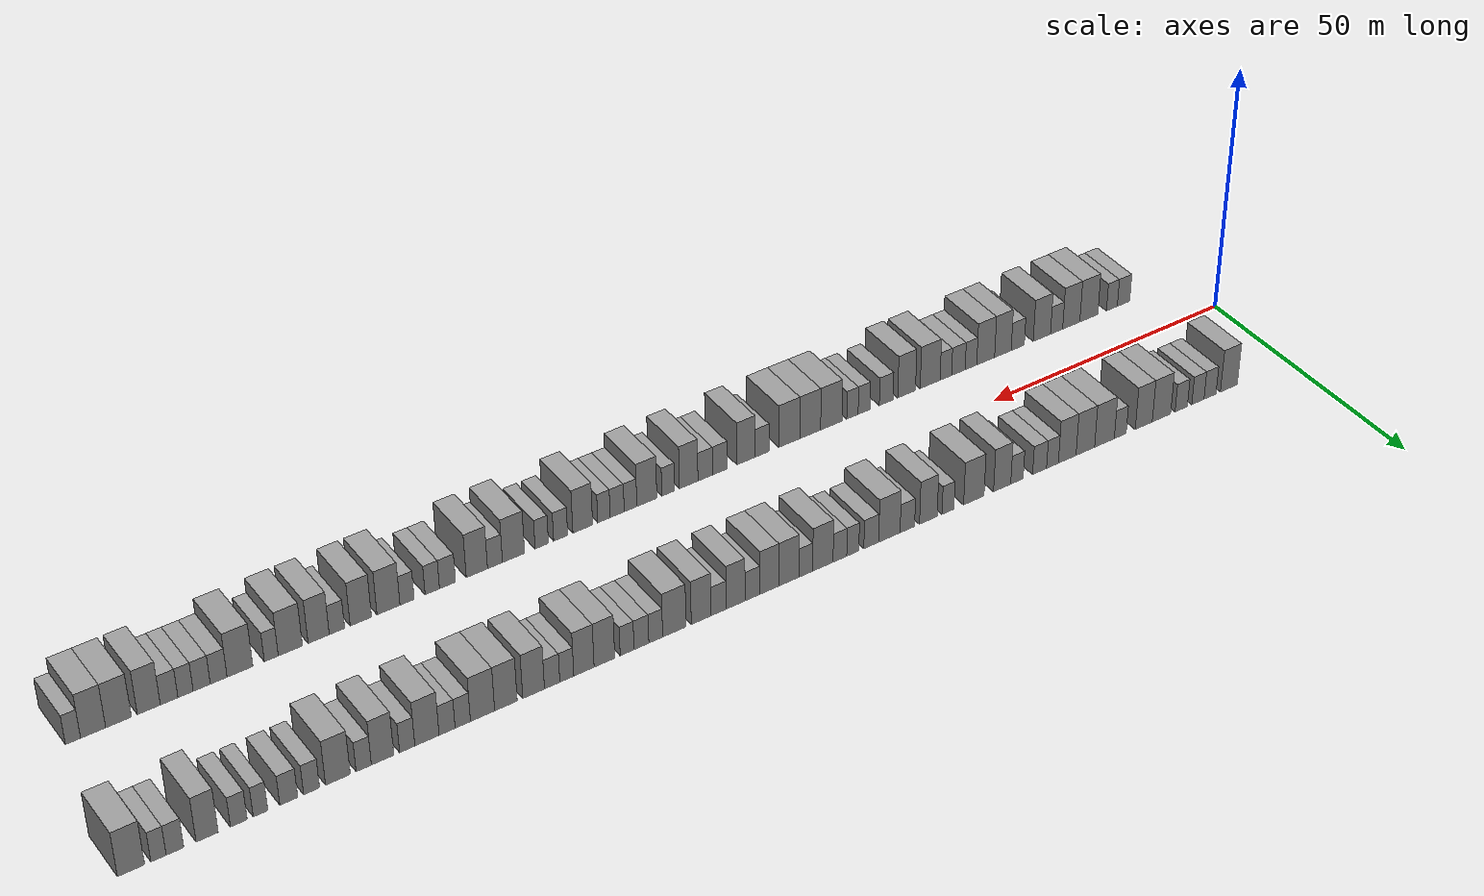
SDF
<sdf version="1.6">
 <world name="default">
  <scene>
   <sky><clouds><speed>12</speed></clouds></sky>
   <ambient>0.4 0.4 0.4 1</ambient>
   <background>0.7 0.7 0.7 1</background>
   <shadows>1</shadows>
  </scene>
  <gravity>0 0 -9.8066</gravity>
  <magnetic_field>6e-06 2.3e-05 -4.2e-05</magnetic_field>
  <physics default="0" name="default_physics" type="ode">
   <ode>
    <solver>
     <type>quick</type>
     <iters>10</iters>
     <sor>1.0</sor>
     <use_dynamic_moi_rescaling>0</use_dynamic_moi_rescaling>
    </solver>
    <constraints>
     <cfm>0</cfm>
     <erp>0.2</erp>
     <contact_max_correcting_vel>100</contact_max_correcting_vel>
     <contact_surface_layer>0.001</contact_surface_layer>
    </constraints>
   </ode>
   <max_step_size>0.004</max_step_size>
   <real_time_factor>1</real_time_factor>
   <real_time_update_rate>250</real_time_update_rate>
  </physics>
  <light name="sun" type="directional">
   <pose>0 0 10 0 0 0</pose>
   <diffuse>0.8 0.8 0.8 1</diffuse>
   <specular>0.2 0.2 0.2 1</specular>
   <attenuation>
    <range>1000</range>
    <constant>0.9</constant>
    <linear>0.01</linear>
    <quadratic>0.001</quadratic>
   </attenuation>
   <direction>-0.5 0.1 -0.9</direction>
  </light>
  <model name="building_1">
   <static>1</static>
   <pose>13.9226 15.0000 0 0.000000 0.000000 1.570796</pose>
   <link name="link">
    <pose>0 0 4.50 0 0 0</pose>
    <collision name="collision"><geometry><box><size>10.0000 3.8453 9.0000</size></box></geometry></collision>
    <visual name="visual">
     <cast_shadows>0</cast_shadows>
     <geometry><box><size>10.0000 3.8453 9.0000</size></box></geometry>
     <material>
      <script>
       <uri>model://grey_wall/materials/scripts</uri>
       <uri>model://grey_wall/materials/textures</uri>
       <name>vrc/grey_wall</name>
      </script>
     </material>
    </visual>
   </link>
  </model>
  <model name="building_2">
   <static>1</static>
   <pose>18.2007 15.0000 0 0.000000 0.000000 1.570796</pose>
   <link name="link">
    <pose>0 0 3.00 0 0 0</pose>
    <collision name="collision"><geometry><box><size>10.0000 2.7110 6.0000</size></box></geometry></collision>
    <visual name="visual">
     <cast_shadows>0</cast_shadows>
     <geometry><box><size>10.0000 2.7110 6.0000</size></box></geometry>
     <material>
      <script>
       <uri>model://grey_wall/materials/scripts</uri>
       <uri>model://grey_wall/materials/textures</uri>
       <name>vrc/grey_wall</name>
      </script>
     </material>
    </visual>
   </link>
  </model>
  <model name="building_3">
   <static>1</static>
   <pose>20.9321 15.0000 0 0.000000 0.000000 1.570796</pose>
   <link name="link">
    <pose>0 0 3.00 0 0 0</pose>
    <collision name="collision"><geometry><box><size>10.0000 2.7518 6.0000</size></box></geometry></collision>
    <visual name="visual">
     <cast_shadows>0</cast_shadows>
     <geometry><box><size>10.0000 2.7518 6.0000</size></box></geometry>
     <material>
      <script>
       <uri>model://grey_wall/materials/scripts</uri>
       <uri>model://grey_wall/materials/textures</uri>
       <name>vrc/grey_wall</name>
      </script>
     </material>
    </visual>
   </link>
  </model>
  <model name="building_4">
   <static>1</static>
   <pose>24.6770 15.0000 0 0.000000 0.000000 1.570796</pose>
   <link name="link">
    <pose>0 0 3.00 0 0 0</pose>
    <collision name="collision"><geometry><box><size>10.0000 2.7379 6.0000</size></box></geometry></collision>
    <visual name="visual">
     <cast_shadows>0</cast_shadows>
     <geometry><box><size>10.0000 2.7379 6.0000</size></box></geometry>
     <material>
      <script>
       <uri>model://grey_wall/materials/scripts</uri>
       <uri>model://grey_wall/materials/textures</uri>
       <name>vrc/grey_wall</name>
      </script>
     </material>
    </visual>
   </link>
  </model>
  <model name="building_5">
   <static>1</static>
   <pose>29.0868 15.0000 0 0.000000 0.000000 1.570796</pose>
   <link name="link">
    <pose>0 0 4.50 0 0 0</pose>
    <collision name="collision"><geometry><box><size>10.0000 4.0817 9.0000</size></box></geometry></collision>
    <visual name="visual">
     <cast_shadows>0</cast_shadows>
     <geometry><box><size>10.0000 4.0817 9.0000</size></box></geometry>
     <material>
      <script>
       <uri>model://grey_wall/materials/scripts</uri>
       <uri>model://grey_wall/materials/textures</uri>
       <name>vrc/grey_wall</name>
      </script>
     </material>
    </visual>
   </link>
  </model>
  <model name="building_6">
   <static>1</static>
   <pose>33.0017 15.0000 0 0.000000 0.000000 1.570796</pose>
   <link name="link">
    <pose>0 0 4.50 0 0 0</pose>
    <collision name="collision"><geometry><box><size>10.0000 3.7479 9.0000</size></box></geometry></collision>
    <visual name="visual">
     <cast_shadows>0</cast_shadows>
     <geometry><box><size>10.0000 3.7479 9.0000</size></box></geometry>
     <material>
      <script>
       <uri>model://grey_wall/materials/scripts</uri>
       <uri>model://grey_wall/materials/textures</uri>
       <name>vrc/grey_wall</name>
      </script>
     </material>
    </visual>
   </link>
  </model>
  <model name="building_7">
   <static>1</static>
   <pose>38.1766 15.0000 0 0.000000 0.000000 1.570796</pose>
   <link name="link">
    <pose>0 0 3.00 0 0 0</pose>
    <collision name="collision"><geometry><box><size>10.0000 2.6020 6.0000</size></box></geometry></collision>
    <visual name="visual">
     <cast_shadows>0</cast_shadows>
     <geometry><box><size>10.0000 2.6020 6.0000</size></box></geometry>
     <material>
      <script>
       <uri>model://grey_wall/materials/scripts</uri>
       <uri>model://grey_wall/materials/textures</uri>
       <name>vrc/grey_wall</name>
      </script>
     </material>
    </visual>
   </link>
  </model>
  <model name="building_8">
   <static>1</static>
   <pose>41.6271 15.0000 0 0.000000 0.000000 1.570796</pose>
   <link name="link">
    <pose>0 0 4.50 0 0 0</pose>
    <collision name="collision"><geometry><box><size>10.0000 4.2989 9.0000</size></box></geometry></collision>
    <visual name="visual">
     <cast_shadows>0</cast_shadows>
     <geometry><box><size>10.0000 4.2989 9.0000</size></box></geometry>
     <material>
      <script>
       <uri>model://grey_wall/materials/scripts</uri>
       <uri>model://grey_wall/materials/textures</uri>
       <name>vrc/grey_wall</name>
      </script>
     </material>
    </visual>
   </link>
  </model>
  <model name="building_9">
   <static>1</static>
   <pose>45.7848 15.0000 0 0.000000 0.000000 1.570796</pose>
   <link name="link">
    <pose>0 0 4.50 0 0 0</pose>
    <collision name="collision"><geometry><box><size>10.0000 4.0166 9.0000</size></box></geometry></collision>
    <visual name="visual">
     <cast_shadows>0</cast_shadows>
     <geometry><box><size>10.0000 4.0166 9.0000</size></box></geometry>
     <material>
      <script>
       <uri>model://grey_wall/materials/scripts</uri>
       <uri>model://grey_wall/materials/textures</uri>
       <name>vrc/grey_wall</name>
      </script>
     </material>
    </visual>
   </link>
  </model>
  <model name="building_10">
   <static>1</static>
   <pose>49.6950 15.0000 0 0.000000 0.000000 1.570796</pose>
   <link name="link">
    <pose>0 0 4.50 0 0 0</pose>
    <collision name="collision"><geometry><box><size>10.0000 3.8036 9.0000</size></box></geometry></collision>
    <visual name="visual">
     <cast_shadows>0</cast_shadows>
     <geometry><box><size>10.0000 3.8036 9.0000</size></box></geometry>
     <material>
      <script>
       <uri>model://grey_wall/materials/scripts</uri>
       <uri>model://grey_wall/materials/textures</uri>
       <name>vrc/grey_wall</name>
      </script>
     </material>
    </visual>
   </link>
  </model>
  <model name="building_11">
   <static>1</static>
   <pose>52.8609 15.0000 0 0.000000 0.000000 1.570796</pose>
   <link name="link">
    <pose>0 0 3.00 0 0 0</pose>
    <collision name="collision"><geometry><box><size>10.0000 2.5283 6.0000</size></box></geometry></collision>
    <visual name="visual">
     <cast_shadows>0</cast_shadows>
     <geometry><box><size>10.0000 2.5283 6.0000</size></box></geometry>
     <material>
      <script>
       <uri>model://grey_wall/materials/scripts</uri>
       <uri>model://grey_wall/materials/textures</uri>
       <name>vrc/grey_wall</name>
      </script>
     </material>
    </visual>
   </link>
  </model>
  <model name="building_12">
   <static>1</static>
   <pose>55.6068 15.0000 0 0.000000 0.000000 1.570796</pose>
   <link name="link">
    <pose>0 0 3.00 0 0 0</pose>
    <collision name="collision"><geometry><box><size>10.0000 2.9635 6.0000</size></box></geometry></collision>
    <visual name="visual">
     <cast_shadows>0</cast_shadows>
     <geometry><box><size>10.0000 2.9635 6.0000</size></box></geometry>
     <material>
      <script>
       <uri>model://grey_wall/materials/scripts</uri>
       <uri>model://grey_wall/materials/textures</uri>
       <name>vrc/grey_wall</name>
      </script>
     </material>
    </visual>
   </link>
  </model>
  <model name="building_13">
   <static>1</static>
   <pose>60.4055 15.0000 0 0.000000 0.000000 1.570796</pose>
   <link name="link">
    <pose>0 0 3.00 0 0 0</pose>
    <collision name="collision"><geometry><box><size>10.0000 2.6340 6.0000</size></box></geometry></collision>
    <visual name="visual">
     <cast_shadows>0</cast_shadows>
     <geometry><box><size>10.0000 2.6340 6.0000</size></box></geometry>
     <material>
      <script>
       <uri>model://grey_wall/materials/scripts</uri>
       <uri>model://grey_wall/materials/textures</uri>
       <name>vrc/grey_wall</name>
      </script>
     </material>
    </visual>
   </link>
  </model>
  <model name="building_14">
   <static>1</static>
   <pose>63.5333 15.0000 0 0.000000 0.000000 1.570796</pose>
   <link name="link">
    <pose>0 0 4.50 0 0 0</pose>
    <collision name="collision"><geometry><box><size>10.0000 3.6216 9.0000</size></box></geometry></collision>
    <visual name="visual">
     <cast_shadows>0</cast_shadows>
     <geometry><box><size>10.0000 3.6216 9.0000</size></box></geometry>
     <material>
      <script>
       <uri>model://grey_wall/materials/scripts</uri>
       <uri>model://grey_wall/materials/textures</uri>
       <name>vrc/grey_wall</name>
      </script>
     </material>
    </visual>
   </link>
  </model>
  <model name="building_15">
   <static>1</static>
   <pose>69.4708 15.0000 0 0.000000 0.000000 1.570796</pose>
   <link name="link">
    <pose>0 0 4.50 0 0 0</pose>
    <collision name="collision"><geometry><box><size>10.0000 4.2534 9.0000</size></box></geometry></collision>
    <visual name="visual">
     <cast_shadows>0</cast_shadows>
     <geometry><box><size>10.0000 4.2534 9.0000</size></box></geometry>
     <material>
      <script>
       <uri>model://grey_wall/materials/scripts</uri>
       <uri>model://grey_wall/materials/textures</uri>
       <name>vrc/grey_wall</name>
      </script>
     </material>
    </visual>
   </link>
  </model>
  <model name="building_16">
   <static>1</static>
   <pose>74.8315 15.0000 0 0.000000 0.000000 1.570796</pose>
   <link name="link">
    <pose>0 0 3.00 0 0 0</pose>
    <collision name="collision"><geometry><box><size>10.0000 2.4681 6.0000</size></box></geometry></collision>
    <visual name="visual">
     <cast_shadows>0</cast_shadows>
     <geometry><box><size>10.0000 2.4681 6.0000</size></box></geometry>
     <material>
      <script>
       <uri>model://grey_wall/materials/scripts</uri>
       <uri>model://grey_wall/materials/textures</uri>
       <name>vrc/grey_wall</name>
      </script>
     </material>
    </visual>
   </link>
  </model>
  <model name="building_17">
   <static>1</static>
   <pose>78.8737 15.0000 0 0.000000 0.000000 1.570796</pose>
   <link name="link">
    <pose>0 0 4.50 0 0 0</pose>
    <collision name="collision"><geometry><box><size>10.0000 3.6162 9.0000</size></box></geometry></collision>
    <visual name="visual">
     <cast_shadows>0</cast_shadows>
     <geometry><box><size>10.0000 3.6162 9.0000</size></box></geometry>
     <material>
      <script>
       <uri>model://grey_wall/materials/scripts</uri>
       <uri>model://grey_wall/materials/textures</uri>
       <name>vrc/grey_wall</name>
      </script>
     </material>
    </visual>
   </link>
  </model>
  <model name="building_18">
   <static>1</static>
   <pose>83.1581 15.0000 0 0.000000 0.000000 1.570796</pose>
   <link name="link">
    <pose>0 0 3.00 0 0 0</pose>
    <collision name="collision"><geometry><box><size>10.0000 2.9525 6.0000</size></box></geometry></collision>
    <visual name="visual">
     <cast_shadows>0</cast_shadows>
     <geometry><box><size>10.0000 2.9525 6.0000</size></box></geometry>
     <material>
      <script>
       <uri>model://grey_wall/materials/scripts</uri>
       <uri>model://grey_wall/materials/textures</uri>
       <name>vrc/grey_wall</name>
      </script>
     </material>
    </visual>
   </link>
  </model>
  <model name="building_19">
   <static>1</static>
   <pose>86.7985 15.0000 0 0.000000 0.000000 1.570796</pose>
   <link name="link">
    <pose>0 0 4.50 0 0 0</pose>
    <collision name="collision"><geometry><box><size>10.0000 4.3284 9.0000</size></box></geometry></collision>
    <visual name="visual">
     <cast_shadows>0</cast_shadows>
     <geometry><box><size>10.0000 4.3284 9.0000</size></box></geometry>
     <material>
      <script>
       <uri>model://grey_wall/materials/scripts</uri>
       <uri>model://grey_wall/materials/textures</uri>
       <name>vrc/grey_wall</name>
      </script>
     </material>
    </visual>
   </link>
  </model>
  <model name="building_20">
   <static>1</static>
   <pose>90.4593 15.0000 0 0.000000 0.000000 1.570796</pose>
   <link name="link">
    <pose>0 0 3.00 0 0 0</pose>
    <collision name="collision"><geometry><box><size>10.0000 2.9933 6.0000</size></box></geometry></collision>
    <visual name="visual">
     <cast_shadows>0</cast_shadows>
     <geometry><box><size>10.0000 2.9933 6.0000</size></box></geometry>
     <material>
      <script>
       <uri>model://grey_wall/materials/scripts</uri>
       <uri>model://grey_wall/materials/textures</uri>
       <name>vrc/grey_wall</name>
      </script>
     </material>
    </visual>
   </link>
  </model>
  <model name="building_21">
   <static>1</static>
   <pose>94.1721 15.0000 0 0.000000 0.000000 1.570796</pose>
   <link name="link">
    <pose>0 0 3.00 0 0 0</pose>
    <collision name="collision"><geometry><box><size>10.0000 2.4321 6.0000</size></box></geometry></collision>
    <visual name="visual">
     <cast_shadows>0</cast_shadows>
     <geometry><box><size>10.0000 2.4321 6.0000</size></box></geometry>
     <material>
      <script>
       <uri>model://grey_wall/materials/scripts</uri>
       <uri>model://grey_wall/materials/textures</uri>
       <name>vrc/grey_wall</name>
      </script>
     </material>
    </visual>
   </link>
  </model>
  <model name="building_22">
   <static>1</static>
   <pose>96.7443 15.0000 0 0.000000 0.000000 1.570796</pose>
   <link name="link">
    <pose>0 0 3.00 0 0 0</pose>
    <collision name="collision"><geometry><box><size>10.0000 2.7123 6.0000</size></box></geometry></collision>
    <visual name="visual">
     <cast_shadows>0</cast_shadows>
     <geometry><box><size>10.0000 2.7123 6.0000</size></box></geometry>
     <material>
      <script>
       <uri>model://grey_wall/materials/scripts</uri>
       <uri>model://grey_wall/materials/textures</uri>
       <name>vrc/grey_wall</name>
      </script>
     </material>
    </visual>
   </link>
  </model>
  <model name="building_23">
   <static>1</static>
   <pose>100.1131 15.0000 0 0.000000 0.000000 1.570796</pose>
   <link name="link">
    <pose>0 0 4.50 0 0 0</pose>
    <collision name="collision"><geometry><box><size>10.0000 4.0254 9.0000</size></box></geometry></collision>
    <visual name="visual">
     <cast_shadows>0</cast_shadows>
     <geometry><box><size>10.0000 4.0254 9.0000</size></box></geometry>
     <material>
      <script>
       <uri>model://grey_wall/materials/scripts</uri>
       <uri>model://grey_wall/materials/textures</uri>
       <name>vrc/grey_wall</name>
      </script>
     </material>
    </visual>
   </link>
  </model>
  <model name="building_24">
   <static>1</static>
   <pose>103.4632 15.0000 0 0.000000 0.000000 1.570796</pose>
   <link name="link">
    <pose>0 0 3.00 0 0 0</pose>
    <collision name="collision"><geometry><box><size>10.0000 2.6749 6.0000</size></box></geometry></collision>
    <visual name="visual">
     <cast_shadows>0</cast_shadows>
     <geometry><box><size>10.0000 2.6749 6.0000</size></box></geometry>
     <material>
      <script>
       <uri>model://grey_wall/materials/scripts</uri>
       <uri>model://grey_wall/materials/textures</uri>
       <name>vrc/grey_wall</name>
      </script>
     </material>
    </visual>
   </link>
  </model>
  <model name="building_25">
   <static>1</static>
   <pose>106.7706 15.0000 0 0.000000 0.000000 1.570796</pose>
   <link name="link">
    <pose>0 0 4.50 0 0 0</pose>
    <collision name="collision"><geometry><box><size>10.0000 3.9398 9.0000</size></box></geometry></collision>
    <visual name="visual">
     <cast_shadows>0</cast_shadows>
     <geometry><box><size>10.0000 3.9398 9.0000</size></box></geometry>
     <material>
      <script>
       <uri>model://grey_wall/materials/scripts</uri>
       <uri>model://grey_wall/materials/textures</uri>
       <name>vrc/grey_wall</name>
      </script>
     </material>
    </visual>
   </link>
  </model>
  <model name="building_26">
   <static>1</static>
   <pose>110.5769 15.0000 0 0.000000 0.000000 1.570796</pose>
   <link name="link">
    <pose>0 0 4.50 0 0 0</pose>
    <collision name="collision"><geometry><box><size>10.0000 3.6727 9.0000</size></box></geometry></collision>
    <visual name="visual">
     <cast_shadows>0</cast_shadows>
     <geometry><box><size>10.0000 3.6727 9.0000</size></box></geometry>
     <material>
      <script>
       <uri>model://grey_wall/materials/scripts</uri>
       <uri>model://grey_wall/materials/textures</uri>
       <name>vrc/grey_wall</name>
      </script>
     </material>
    </visual>
   </link>
  </model>
  <model name="building_27">
   <static>1</static>
   <pose>113.8792 15.0000 0 0.000000 0.000000 1.570796</pose>
   <link name="link">
    <pose>0 0 3.00 0 0 0</pose>
    <collision name="collision"><geometry><box><size>10.0000 2.9318 6.0000</size></box></geometry></collision>
    <visual name="visual">
     <cast_shadows>0</cast_shadows>
     <geometry><box><size>10.0000 2.9318 6.0000</size></box></geometry>
     <material>
      <script>
       <uri>model://grey_wall/materials/scripts</uri>
       <uri>model://grey_wall/materials/textures</uri>
       <name>vrc/grey_wall</name>
      </script>
     </material>
    </visual>
   </link>
  </model>
  <model name="building_28">
   <static>1</static>
   <pose>117.1531 15.0000 0 0.000000 0.000000 1.570796</pose>
   <link name="link">
    <pose>0 0 4.50 0 0 0</pose>
    <collision name="collision"><geometry><box><size>10.0000 3.6159 9.0000</size></box></geometry></collision>
    <visual name="visual">
     <cast_shadows>0</cast_shadows>
     <geometry><box><size>10.0000 3.6159 9.0000</size></box></geometry>
     <material>
      <script>
       <uri>model://grey_wall/materials/scripts</uri>
       <uri>model://grey_wall/materials/textures</uri>
       <name>vrc/grey_wall</name>
      </script>
     </material>
    </visual>
   </link>
  </model>
  <model name="building_29">
   <static>1</static>
   <pose>120.4234 15.0000 0 0.000000 0.000000 1.570796</pose>
   <link name="link">
    <pose>0 0 3.00 0 0 0</pose>
    <collision name="collision"><geometry><box><size>10.0000 2.9247 6.0000</size></box></geometry></collision>
    <visual name="visual">
     <cast_shadows>0</cast_shadows>
     <geometry><box><size>10.0000 2.9247 6.0000</size></box></geometry>
     <material>
      <script>
       <uri>model://grey_wall/materials/scripts</uri>
       <uri>model://grey_wall/materials/textures</uri>
       <name>vrc/grey_wall</name>
      </script>
     </material>
    </visual>
   </link>
  </model>
  <model name="building_30">
   <static>1</static>
   <pose>123.7611 15.0000 0 0.000000 0.000000 1.570796</pose>
   <link name="link">
    <pose>0 0 4.50 0 0 0</pose>
    <collision name="collision"><geometry><box><size>10.0000 3.7508 9.0000</size></box></geometry></collision>
    <visual name="visual">
     <cast_shadows>0</cast_shadows>
     <geometry><box><size>10.0000 3.7508 9.0000</size></box></geometry>
     <material>
      <script>
       <uri>model://grey_wall/materials/scripts</uri>
       <uri>model://grey_wall/materials/textures</uri>
       <name>vrc/grey_wall</name>
      </script>
     </material>
    </visual>
   </link>
  </model>
  <model name="building_31">
   <static>1</static>
   <pose>128.8408 15.0000 0 0.000000 0.000000 1.570796</pose>
   <link name="link">
    <pose>0 0 4.50 0 0 0</pose>
    <collision name="collision"><geometry><box><size>10.0000 4.4086 9.0000</size></box></geometry></collision>
    <visual name="visual">
     <cast_shadows>0</cast_shadows>
     <geometry><box><size>10.0000 4.4086 9.0000</size></box></geometry>
     <material>
      <script>
       <uri>model://grey_wall/materials/scripts</uri>
       <uri>model://grey_wall/materials/textures</uri>
       <name>vrc/grey_wall</name>
      </script>
     </material>
    </visual>
   </link>
  </model>
  <model name="building_32">
   <static>1</static>
   <pose>132.3393 15.0000 0 0.000000 0.000000 1.570796</pose>
   <link name="link">
    <pose>0 0 3.00 0 0 0</pose>
    <collision name="collision"><geometry><box><size>10.0000 2.5883 6.0000</size></box></geometry></collision>
    <visual name="visual">
     <cast_shadows>0</cast_shadows>
     <geometry><box><size>10.0000 2.5883 6.0000</size></box></geometry>
     <material>
      <script>
       <uri>model://grey_wall/materials/scripts</uri>
       <uri>model://grey_wall/materials/textures</uri>
       <name>vrc/grey_wall</name>
      </script>
     </material>
    </visual>
   </link>
  </model>
  <model name="building_33">
   <static>1</static>
   <pose>135.0188 15.0000 0 0.000000 0.000000 1.570796</pose>
   <link name="link">
    <pose>0 0 3.00 0 0 0</pose>
    <collision name="collision"><geometry><box><size>10.0000 2.7707 6.0000</size></box></geometry></collision>
    <visual name="visual">
     <cast_shadows>0</cast_shadows>
     <geometry><box><size>10.0000 2.7707 6.0000</size></box></geometry>
     <material>
      <script>
       <uri>model://grey_wall/materials/scripts</uri>
       <uri>model://grey_wall/materials/textures</uri>
       <name>vrc/grey_wall</name>
      </script>
     </material>
    </visual>
   </link>
  </model>
  <model name="building_34">
   <static>1</static>
   <pose>137.6904 15.0000 0 0.000000 0.000000 1.570796</pose>
   <link name="link">
    <pose>0 0 3.00 0 0 0</pose>
    <collision name="collision"><geometry><box><size>10.0000 2.5725 6.0000</size></box></geometry></collision>
    <visual name="visual">
     <cast_shadows>0</cast_shadows>
     <geometry><box><size>10.0000 2.5725 6.0000</size></box></geometry>
     <material>
      <script>
       <uri>model://grey_wall/materials/scripts</uri>
       <uri>model://grey_wall/materials/textures</uri>
       <name>vrc/grey_wall</name>
      </script>
     </material>
    </visual>
   </link>
  </model>
  <model name="building_35">
   <static>1</static>
   <pose>141.8845 15.0000 0 0.000000 0.000000 1.570796</pose>
   <link name="link">
    <pose>0 0 4.50 0 0 0</pose>
    <collision name="collision"><geometry><box><size>10.0000 3.8157 9.0000</size></box></geometry></collision>
    <visual name="visual">
     <cast_shadows>0</cast_shadows>
     <geometry><box><size>10.0000 3.8157 9.0000</size></box></geometry>
     <material>
      <script>
       <uri>model://grey_wall/materials/scripts</uri>
       <uri>model://grey_wall/materials/textures</uri>
       <name>vrc/grey_wall</name>
      </script>
     </material>
    </visual>
   </link>
  </model>
  <model name="building_36">
   <static>1</static>
   <pose>145.6510 15.0000 0 0.000000 0.000000 1.570796</pose>
   <link name="link">
    <pose>0 0 4.50 0 0 0</pose>
    <collision name="collision"><geometry><box><size>10.0000 3.7173 9.0000</size></box></geometry></collision>
    <visual name="visual">
     <cast_shadows>0</cast_shadows>
     <geometry><box><size>10.0000 3.7173 9.0000</size></box></geometry>
     <material>
      <script>
       <uri>model://grey_wall/materials/scripts</uri>
       <uri>model://grey_wall/materials/textures</uri>
       <name>vrc/grey_wall</name>
      </script>
     </material>
    </visual>
   </link>
  </model>
  <model name="building_37">
   <static>1</static>
   <pose>148.7827 15.0000 0 0.000000 0.000000 1.570796</pose>
   <link name="link">
    <pose>0 0 3.00 0 0 0</pose>
    <collision name="collision"><geometry><box><size>10.0000 2.5460 6.0000</size></box></geometry></collision>
    <visual name="visual">
     <cast_shadows>0</cast_shadows>
     <geometry><box><size>10.0000 2.5460 6.0000</size></box></geometry>
     <material>
      <script>
       <uri>model://grey_wall/materials/scripts</uri>
       <uri>model://grey_wall/materials/textures</uri>
       <name>vrc/grey_wall</name>
      </script>
     </material>
    </visual>
   </link>
  </model>
  <model name="building_38">
   <static>1</static>
   <pose>151.4500 15.0000 0 0.000000 0.000000 1.570796</pose>
   <link name="link">
    <pose>0 0 3.00 0 0 0</pose>
    <collision name="collision"><geometry><box><size>10.0000 2.7886 6.0000</size></box></geometry></collision>
    <visual name="visual">
     <cast_shadows>0</cast_shadows>
     <geometry><box><size>10.0000 2.7886 6.0000</size></box></geometry>
     <material>
      <script>
       <uri>model://grey_wall/materials/scripts</uri>
       <uri>model://grey_wall/materials/textures</uri>
       <name>vrc/grey_wall</name>
      </script>
     </material>
    </visual>
   </link>
  </model>
  <model name="building_39">
   <static>1</static>
   <pose>154.8027 15.0000 0 0.000000 0.000000 1.570796</pose>
   <link name="link">
    <pose>0 0 4.50 0 0 0</pose>
    <collision name="collision"><geometry><box><size>10.0000 3.9167 9.0000</size></box></geometry></collision>
    <visual name="visual">
     <cast_shadows>0</cast_shadows>
     <geometry><box><size>10.0000 3.9167 9.0000</size></box></geometry>
     <material>
      <script>
       <uri>model://grey_wall/materials/scripts</uri>
       <uri>model://grey_wall/materials/textures</uri>
       <name>vrc/grey_wall</name>
      </script>
     </material>
    </visual>
   </link>
  </model>
  <model name="building_40">
   <static>1</static>
   <pose>159.7739 15.0000 0 0.000000 0.000000 1.570796</pose>
   <link name="link">
    <pose>0 0 4.50 0 0 0</pose>
    <collision name="collision"><geometry><box><size>10.0000 4.0258 9.0000</size></box></geometry></collision>
    <visual name="visual">
     <cast_shadows>0</cast_shadows>
     <geometry><box><size>10.0000 4.0258 9.0000</size></box></geometry>
     <material>
      <script>
       <uri>model://grey_wall/materials/scripts</uri>
       <uri>model://grey_wall/materials/textures</uri>
       <name>vrc/grey_wall</name>
      </script>
     </material>
    </visual>
   </link>
  </model>
  <model name="building_41">
   <static>1</static>
   <pose>163.9372 15.0000 0 0.000000 0.000000 1.570796</pose>
   <link name="link">
    <pose>0 0 4.50 0 0 0</pose>
    <collision name="collision"><geometry><box><size>10.0000 4.3008 9.0000</size></box></geometry></collision>
    <visual name="visual">
     <cast_shadows>0</cast_shadows>
     <geometry><box><size>10.0000 4.3008 9.0000</size></box></geometry>
     <material>
      <script>
       <uri>model://grey_wall/materials/scripts</uri>
       <uri>model://grey_wall/materials/textures</uri>
       <name>vrc/grey_wall</name>
      </script>
     </material>
    </visual>
   </link>
  </model>
  <model name="building_42">
   <static>1</static>
   <pose>167.4386 15.0000 0 0.000000 0.000000 1.570796</pose>
   <link name="link">
    <pose>0 0 3.00 0 0 0</pose>
    <collision name="collision"><geometry><box><size>10.0000 2.7020 6.0000</size></box></geometry></collision>
    <visual name="visual">
     <cast_shadows>0</cast_shadows>
     <geometry><box><size>10.0000 2.7020 6.0000</size></box></geometry>
     <material>
      <script>
       <uri>model://grey_wall/materials/scripts</uri>
       <uri>model://grey_wall/materials/textures</uri>
       <name>vrc/grey_wall</name>
      </script>
     </material>
    </visual>
   </link>
  </model>
  <model name="building_43">
   <static>1</static>
   <pose>170.1975 15.0000 0 0.000000 0.000000 1.570796</pose>
   <link name="link">
    <pose>0 0 3.00 0 0 0</pose>
    <collision name="collision"><geometry><box><size>10.0000 2.8158 6.0000</size></box></geometry></collision>
    <visual name="visual">
     <cast_shadows>0</cast_shadows>
     <geometry><box><size>10.0000 2.8158 6.0000</size></box></geometry>
     <material>
      <script>
       <uri>model://grey_wall/materials/scripts</uri>
       <uri>model://grey_wall/materials/textures</uri>
       <name>vrc/grey_wall</name>
      </script>
     </material>
    </visual>
   </link>
  </model>
  <model name="building_44">
   <static>1</static>
   <pose>173.7236 15.0000 0 0.000000 0.000000 1.570796</pose>
   <link name="link">
    <pose>0 0 4.50 0 0 0</pose>
    <collision name="collision"><geometry><box><size>10.0000 4.2362 9.0000</size></box></geometry></collision>
    <visual name="visual">
     <cast_shadows>0</cast_shadows>
     <geometry><box><size>10.0000 4.2362 9.0000</size></box></geometry>
     <material>
      <script>
       <uri>model://grey_wall/materials/scripts</uri>
       <uri>model://grey_wall/materials/textures</uri>
       <name>vrc/grey_wall</name>
      </script>
     </material>
    </visual>
   </link>
  </model>
  <model name="building_45">
   <static>1</static>
   <pose>177.1646 15.0000 0 0.000000 0.000000 1.570796</pose>
   <link name="link">
    <pose>0 0 3.00 0 0 0</pose>
    <collision name="collision"><geometry><box><size>10.0000 2.6458 6.0000</size></box></geometry></collision>
    <visual name="visual">
     <cast_shadows>0</cast_shadows>
     <geometry><box><size>10.0000 2.6458 6.0000</size></box></geometry>
     <material>
      <script>
       <uri>model://grey_wall/materials/scripts</uri>
       <uri>model://grey_wall/materials/textures</uri>
       <name>vrc/grey_wall</name>
      </script>
     </material>
    </visual>
   </link>
  </model>
  <model name="building_46">
   <static>1</static>
   <pose>181.4121 15.0000 0 0.000000 0.000000 1.570796</pose>
   <link name="link">
    <pose>0 0 4.50 0 0 0</pose>
    <collision name="collision"><geometry><box><size>10.0000 3.8492 9.0000</size></box></geometry></collision>
    <visual name="visual">
     <cast_shadows>0</cast_shadows>
     <geometry><box><size>10.0000 3.8492 9.0000</size></box></geometry>
     <material>
      <script>
       <uri>model://grey_wall/materials/scripts</uri>
       <uri>model://grey_wall/materials/textures</uri>
       <name>vrc/grey_wall</name>
      </script>
     </material>
    </visual>
   </link>
  </model>
  <model name="building_47">
   <static>1</static>
   <pose>184.6428 15.0000 0 0.000000 0.000000 1.570796</pose>
   <link name="link">
    <pose>0 0 3.00 0 0 0</pose>
    <collision name="collision"><geometry><box><size>10.0000 2.6121 6.0000</size></box></geometry></collision>
    <visual name="visual">
     <cast_shadows>0</cast_shadows>
     <geometry><box><size>10.0000 2.6121 6.0000</size></box></geometry>
     <material>
      <script>
       <uri>model://grey_wall/materials/scripts</uri>
       <uri>model://grey_wall/materials/textures</uri>
       <name>vrc/grey_wall</name>
      </script>
     </material>
    </visual>
   </link>
  </model>
  <model name="building_48">
   <static>1</static>
   <pose>189.0497 15.0000 0 0.000000 0.000000 1.570796</pose>
   <link name="link">
    <pose>0 0 4.50 0 0 0</pose>
    <collision name="collision"><geometry><box><size>10.0000 4.2017 9.0000</size></box></geometry></collision>
    <visual name="visual">
     <cast_shadows>0</cast_shadows>
     <geometry><box><size>10.0000 4.2017 9.0000</size></box></geometry>
     <material>
      <script>
       <uri>model://grey_wall/materials/scripts</uri>
       <uri>model://grey_wall/materials/textures</uri>
       <name>vrc/grey_wall</name>
      </script>
     </material>
    </visual>
   </link>
  </model>
  <model name="building_49">
   <static>1</static>
   <pose>193.4907 15.0000 0 0.000000 0.000000 1.570796</pose>
   <link name="link">
    <pose>0 0 3.00 0 0 0</pose>
    <collision name="collision"><geometry><box><size>10.0000 2.6802 6.0000</size></box></geometry></collision>
    <visual name="visual">
     <cast_shadows>0</cast_shadows>
     <geometry><box><size>10.0000 2.6802 6.0000</size></box></geometry>
     <material>
      <script>
       <uri>model://grey_wall/materials/scripts</uri>
       <uri>model://grey_wall/materials/textures</uri>
       <name>vrc/grey_wall</name>
      </script>
     </material>
    </visual>
   </link>
  </model>
  <model name="building_50">
   <static>1</static>
   <pose>197.3285 15.0000 0 0.000000 0.000000 1.570796</pose>
   <link name="link">
    <pose>0 0 3.00 0 0 0</pose>
    <collision name="collision"><geometry><box><size>10.0000 2.9954 6.0000</size></box></geometry></collision>
    <visual name="visual">
     <cast_shadows>0</cast_shadows>
     <geometry><box><size>10.0000 2.9954 6.0000</size></box></geometry>
     <material>
      <script>
       <uri>model://grey_wall/materials/scripts</uri>
       <uri>model://grey_wall/materials/textures</uri>
       <name>vrc/grey_wall</name>
      </script>
     </material>
    </visual>
   </link>
  </model>
  <model name="building_51">
   <static>1</static>
   <pose>202.0354 15.0000 0 0.000000 0.000000 1.570796</pose>
   <link name="link">
    <pose>0 0 3.00 0 0 0</pose>
    <collision name="collision"><geometry><box><size>10.0000 2.4184 6.0000</size></box></geometry></collision>
    <visual name="visual">
     <cast_shadows>0</cast_shadows>
     <geometry><box><size>10.0000 2.4184 6.0000</size></box></geometry>
     <material>
      <script>
       <uri>model://grey_wall/materials/scripts</uri>
       <uri>model://grey_wall/materials/textures</uri>
       <name>vrc/grey_wall</name>
      </script>
     </material>
    </visual>
   </link>
  </model>
  <model name="building_52">
   <static>1</static>
   <pose>205.6255 15.0000 0 0.000000 0.000000 1.570796</pose>
   <link name="link">
    <pose>0 0 3.00 0 0 0</pose>
    <collision name="collision"><geometry><box><size>10.0000 2.7619 6.0000</size></box></geometry></collision>
    <visual name="visual">
     <cast_shadows>0</cast_shadows>
     <geometry><box><size>10.0000 2.7619 6.0000</size></box></geometry>
     <material>
      <script>
       <uri>model://grey_wall/materials/scripts</uri>
       <uri>model://grey_wall/materials/textures</uri>
       <name>vrc/grey_wall</name>
      </script>
     </material>
    </visual>
   </link>
  </model>
  <model name="building_53">
   <static>1</static>
   <pose>210.8117 15.0000 0 0.000000 0.000000 1.570796</pose>
   <link name="link">
    <pose>0 0 4.50 0 0 0</pose>
    <collision name="collision"><geometry><box><size>10.0000 3.6105 9.0000</size></box></geometry></collision>
    <visual name="visual">
     <cast_shadows>0</cast_shadows>
     <geometry><box><size>10.0000 3.6105 9.0000</size></box></geometry>
     <material>
      <script>
       <uri>model://grey_wall/materials/scripts</uri>
       <uri>model://grey_wall/materials/textures</uri>
       <name>vrc/grey_wall</name>
      </script>
     </material>
    </visual>
   </link>
  </model>
  <model name="building_54">
   <static>1</static>
   <pose>216.0396 15.0000 0 0.000000 0.000000 1.570796</pose>
   <link name="link">
    <pose>0 0 3.00 0 0 0</pose>
    <collision name="collision"><geometry><box><size>10.0000 2.8452 6.0000</size></box></geometry></collision>
    <visual name="visual">
     <cast_shadows>0</cast_shadows>
     <geometry><box><size>10.0000 2.8452 6.0000</size></box></geometry>
     <material>
      <script>
       <uri>model://grey_wall/materials/scripts</uri>
       <uri>model://grey_wall/materials/textures</uri>
       <name>vrc/grey_wall</name>
      </script>
     </material>
    </visual>
   </link>
  </model>
  <model name="building_55">
   <static>1</static>
   <pose>218.6882 15.0000 0 0.000000 0.000000 1.570796</pose>
   <link name="link">
    <pose>0 0 3.00 0 0 0</pose>
    <collision name="collision"><geometry><box><size>10.0000 2.4521 6.0000</size></box></geometry></collision>
    <visual name="visual">
     <cast_shadows>0</cast_shadows>
     <geometry><box><size>10.0000 2.4521 6.0000</size></box></geometry>
     <material>
      <script>
       <uri>model://grey_wall/materials/scripts</uri>
       <uri>model://grey_wall/materials/textures</uri>
       <name>vrc/grey_wall</name>
      </script>
     </material>
    </visual>
   </link>
  </model>
  <model name="building_56">
   <static>1</static>
   <pose>223.0905 15.0000 0 0.000000 0.000000 1.570796</pose>
   <link name="link">
    <pose>0 0 4.50 0 0 0</pose>
    <collision name="collision"><geometry><box><size>10.0000 4.3525 9.0000</size></box></geometry></collision>
    <visual name="visual">
     <cast_shadows>0</cast_shadows>
     <geometry><box><size>10.0000 4.3525 9.0000</size></box></geometry>
     <material>
      <script>
       <uri>model://grey_wall/materials/scripts</uri>
       <uri>model://grey_wall/materials/textures</uri>
       <name>vrc/grey_wall</name>
      </script>
     </material>
    </visual>
   </link>
  </model>
  <model name="building_57">
   <static>1</static>
   <pose>13.4262 -15.0000 0 0.000000 0.000000 1.570796</pose>
   <link name="link">
    <pose>0 0 3.00 0 0 0</pose>
    <collision name="collision"><geometry><box><size>10.0000 2.8524 6.0000</size></box></geometry></collision>
    <visual name="visual">
     <cast_shadows>0</cast_shadows>
     <geometry><box><size>10.0000 2.8524 6.0000</size></box></geometry>
     <material>
      <script>
       <uri>model://grey_wall/materials/scripts</uri>
       <uri>model://grey_wall/materials/textures</uri>
       <name>vrc/grey_wall</name>
      </script>
     </material>
    </visual>
   </link>
  </model>
  <model name="building_58">
   <static>1</static>
   <pose>16.1058 -15.0000 0 0.000000 0.000000 1.570796</pose>
   <link name="link">
    <pose>0 0 3.00 0 0 0</pose>
    <collision name="collision"><geometry><box><size>10.0000 2.5069 6.0000</size></box></geometry></collision>
    <visual name="visual">
     <cast_shadows>0</cast_shadows>
     <geometry><box><size>10.0000 2.5069 6.0000</size></box></geometry>
     <material>
      <script>
       <uri>model://grey_wall/materials/scripts</uri>
       <uri>model://grey_wall/materials/textures</uri>
       <name>vrc/grey_wall</name>
      </script>
     </material>
    </visual>
   </link>
  </model>
  <model name="building_59">
   <static>1</static>
   <pose>21.4099 -15.0000 0 0.000000 0.000000 1.570796</pose>
   <link name="link">
    <pose>0 0 4.50 0 0 0</pose>
    <collision name="collision"><geometry><box><size>10.0000 4.1012 9.0000</size></box></geometry></collision>
    <visual name="visual">
     <cast_shadows>0</cast_shadows>
     <geometry><box><size>10.0000 4.1012 9.0000</size></box></geometry>
     <material>
      <script>
       <uri>model://grey_wall/materials/scripts</uri>
       <uri>model://grey_wall/materials/textures</uri>
       <name>vrc/grey_wall</name>
      </script>
     </material>
    </visual>
   </link>
  </model>
  <model name="building_60">
   <static>1</static>
   <pose>25.4114 -15.0000 0 0.000000 0.000000 1.570796</pose>
   <link name="link">
    <pose>0 0 4.50 0 0 0</pose>
    <collision name="collision"><geometry><box><size>10.0000 3.9020 9.0000</size></box></geometry></collision>
    <visual name="visual">
     <cast_shadows>0</cast_shadows>
     <geometry><box><size>10.0000 3.9020 9.0000</size></box></geometry>
     <material>
      <script>
       <uri>model://grey_wall/materials/scripts</uri>
       <uri>model://grey_wall/materials/textures</uri>
       <name>vrc/grey_wall</name>
      </script>
     </material>
    </visual>
   </link>
  </model>
  <model name="building_61">
   <static>1</static>
   <pose>28.7406 -15.0000 0 0.000000 0.000000 1.570796</pose>
   <link name="link">
    <pose>0 0 3.00 0 0 0</pose>
    <collision name="collision"><geometry><box><size>10.0000 2.7563 6.0000</size></box></geometry></collision>
    <visual name="visual">
     <cast_shadows>0</cast_shadows>
     <geometry><box><size>10.0000 2.7563 6.0000</size></box></geometry>
     <material>
      <script>
       <uri>model://grey_wall/materials/scripts</uri>
       <uri>model://grey_wall/materials/textures</uri>
       <name>vrc/grey_wall</name>
      </script>
     </material>
    </visual>
   </link>
  </model>
  <model name="building_62">
   <static>1</static>
   <pose>32.0567 -15.0000 0 0.000000 0.000000 1.570796</pose>
   <link name="link">
    <pose>0 0 4.50 0 0 0</pose>
    <collision name="collision"><geometry><box><size>10.0000 3.8760 9.0000</size></box></geometry></collision>
    <visual name="visual">
     <cast_shadows>0</cast_shadows>
     <geometry><box><size>10.0000 3.8760 9.0000</size></box></geometry>
     <material>
      <script>
       <uri>model://grey_wall/materials/scripts</uri>
       <uri>model://grey_wall/materials/textures</uri>
       <name>vrc/grey_wall</name>
      </script>
     </material>
    </visual>
   </link>
  </model>
  <model name="building_63">
   <static>1</static>
   <pose>37.4647 -15.0000 0 0.000000 0.000000 1.570796</pose>
   <link name="link">
    <pose>0 0 3.00 0 0 0</pose>
    <collision name="collision"><geometry><box><size>10.0000 2.9399 6.0000</size></box></geometry></collision>
    <visual name="visual">
     <cast_shadows>0</cast_shadows>
     <geometry><box><size>10.0000 2.9399 6.0000</size></box></geometry>
     <material>
      <script>
       <uri>model://grey_wall/materials/scripts</uri>
       <uri>model://grey_wall/materials/textures</uri>
       <name>vrc/grey_wall</name>
      </script>
     </material>
    </visual>
   </link>
  </model>
  <model name="building_64">
   <static>1</static>
   <pose>40.7712 -15.0000 0 0.000000 0.000000 1.570796</pose>
   <link name="link">
    <pose>0 0 4.50 0 0 0</pose>
    <collision name="collision"><geometry><box><size>10.0000 3.6730 9.0000</size></box></geometry></collision>
    <visual name="visual">
     <cast_shadows>0</cast_shadows>
     <geometry><box><size>10.0000 3.6730 9.0000</size></box></geometry>
     <material>
      <script>
       <uri>model://grey_wall/materials/scripts</uri>
       <uri>model://grey_wall/materials/textures</uri>
       <name>vrc/grey_wall</name>
      </script>
     </material>
    </visual>
   </link>
  </model>
  <model name="building_65">
   <static>1</static>
   <pose>44.5831 -15.0000 0 0.000000 0.000000 1.570796</pose>
   <link name="link">
    <pose>0 0 4.50 0 0 0</pose>
    <collision name="collision"><geometry><box><size>10.0000 3.9509 9.0000</size></box></geometry></collision>
    <visual name="visual">
     <cast_shadows>0</cast_shadows>
     <geometry><box><size>10.0000 3.9509 9.0000</size></box></geometry>
     <material>
      <script>
       <uri>model://grey_wall/materials/scripts</uri>
       <uri>model://grey_wall/materials/textures</uri>
       <name>vrc/grey_wall</name>
      </script>
     </material>
    </visual>
   </link>
  </model>
  <model name="building_66">
   <static>1</static>
   <pose>47.8256 -15.0000 0 0.000000 0.000000 1.570796</pose>
   <link name="link">
    <pose>0 0 3.00 0 0 0</pose>
    <collision name="collision"><geometry><box><size>10.0000 2.5341 6.0000</size></box></geometry></collision>
    <visual name="visual">
     <cast_shadows>0</cast_shadows>
     <geometry><box><size>10.0000 2.5341 6.0000</size></box></geometry>
     <material>
      <script>
       <uri>model://grey_wall/materials/scripts</uri>
       <uri>model://grey_wall/materials/textures</uri>
       <name>vrc/grey_wall</name>
      </script>
     </material>
    </visual>
   </link>
  </model>
  <model name="building_67">
   <static>1</static>
   <pose>50.5772 -15.0000 0 0.000000 0.000000 1.570796</pose>
   <link name="link">
    <pose>0 0 3.00 0 0 0</pose>
    <collision name="collision"><geometry><box><size>10.0000 2.9689 6.0000</size></box></geometry></collision>
    <visual name="visual">
     <cast_shadows>0</cast_shadows>
     <geometry><box><size>10.0000 2.9689 6.0000</size></box></geometry>
     <material>
      <script>
       <uri>model://grey_wall/materials/scripts</uri>
       <uri>model://grey_wall/materials/textures</uri>
       <name>vrc/grey_wall</name>
      </script>
     </material>
    </visual>
   </link>
  </model>
  <model name="building_68">
   <static>1</static>
   <pose>53.3177 -15.0000 0 0.000000 0.000000 1.570796</pose>
   <link name="link">
    <pose>0 0 3.00 0 0 0</pose>
    <collision name="collision"><geometry><box><size>10.0000 2.5122 6.0000</size></box></geometry></collision>
    <visual name="visual">
     <cast_shadows>0</cast_shadows>
     <geometry><box><size>10.0000 2.5122 6.0000</size></box></geometry>
     <material>
      <script>
       <uri>model://grey_wall/materials/scripts</uri>
       <uri>model://grey_wall/materials/textures</uri>
       <name>vrc/grey_wall</name>
      </script>
     </material>
    </visual>
   </link>
  </model>
  <model name="building_69">
   <static>1</static>
   <pose>56.7246 -15.0000 0 0.000000 0.000000 1.570796</pose>
   <link name="link">
    <pose>0 0 4.50 0 0 0</pose>
    <collision name="collision"><geometry><box><size>10.0000 4.3016 9.0000</size></box></geometry></collision>
    <visual name="visual">
     <cast_shadows>0</cast_shadows>
     <geometry><box><size>10.0000 4.3016 9.0000</size></box></geometry>
     <material>
      <script>
       <uri>model://grey_wall/materials/scripts</uri>
       <uri>model://grey_wall/materials/textures</uri>
       <name>vrc/grey_wall</name>
      </script>
     </material>
    </visual>
   </link>
  </model>
  <model name="building_70">
   <static>1</static>
   <pose>61.7794 -15.0000 0 0.000000 0.000000 1.570796</pose>
   <link name="link">
    <pose>0 0 4.50 0 0 0</pose>
    <collision name="collision"><geometry><box><size>10.0000 3.8079 9.0000</size></box></geometry></collision>
    <visual name="visual">
     <cast_shadows>0</cast_shadows>
     <geometry><box><size>10.0000 3.8079 9.0000</size></box></geometry>
     <material>
      <script>
       <uri>model://grey_wall/materials/scripts</uri>
       <uri>model://grey_wall/materials/textures</uri>
       <name>vrc/grey_wall</name>
      </script>
     </material>
    </visual>
   </link>
  </model>
  <model name="building_71">
   <static>1</static>
   <pose>66.1522 -15.0000 0 0.000000 0.000000 1.570796</pose>
   <link name="link">
    <pose>0 0 3.00 0 0 0</pose>
    <collision name="collision"><geometry><box><size>10.0000 2.9377 6.0000</size></box></geometry></collision>
    <visual name="visual">
     <cast_shadows>0</cast_shadows>
     <geometry><box><size>10.0000 2.9377 6.0000</size></box></geometry>
     <material>
      <script>
       <uri>model://grey_wall/materials/scripts</uri>
       <uri>model://grey_wall/materials/textures</uri>
       <name>vrc/grey_wall</name>
      </script>
     </material>
    </visual>
   </link>
  </model>
  <model name="building_72">
   <static>1</static>
   <pose>70.8683 -15.0000 0 0.000000 0.000000 1.570796</pose>
   <link name="link">
    <pose>0 0 3.00 0 0 0</pose>
    <collision name="collision"><geometry><box><size>10.0000 2.4945 6.0000</size></box></geometry></collision>
    <visual name="visual">
     <cast_shadows>0</cast_shadows>
     <geometry><box><size>10.0000 2.4945 6.0000</size></box></geometry>
     <material>
      <script>
       <uri>model://grey_wall/materials/scripts</uri>
       <uri>model://grey_wall/materials/textures</uri>
       <name>vrc/grey_wall</name>
      </script>
     </material>
    </visual>
   </link>
  </model>
  <model name="building_73">
   <static>1</static>
   <pose>73.3175 -15.0000 0 0.000000 0.000000 1.570796</pose>
   <link name="link">
    <pose>0 0 3.00 0 0 0</pose>
    <collision name="collision"><geometry><box><size>10.0000 2.4040 6.0000</size></box></geometry></collision>
    <visual name="visual">
     <cast_shadows>0</cast_shadows>
     <geometry><box><size>10.0000 2.4040 6.0000</size></box></geometry>
     <material>
      <script>
       <uri>model://grey_wall/materials/scripts</uri>
       <uri>model://grey_wall/materials/textures</uri>
       <name>vrc/grey_wall</name>
      </script>
     </material>
    </visual>
   </link>
  </model>
  <model name="building_74">
   <static>1</static>
   <pose>77.7529 -15.0000 0 0.000000 0.000000 1.570796</pose>
   <link name="link">
    <pose>0 0 4.50 0 0 0</pose>
    <collision name="collision"><geometry><box><size>10.0000 4.4667 9.0000</size></box></geometry></collision>
    <visual name="visual">
     <cast_shadows>0</cast_shadows>
     <geometry><box><size>10.0000 4.4667 9.0000</size></box></geometry>
     <material>
      <script>
       <uri>model://grey_wall/materials/scripts</uri>
       <uri>model://grey_wall/materials/textures</uri>
       <name>vrc/grey_wall</name>
      </script>
     </material>
    </visual>
   </link>
  </model>
  <model name="building_75">
   <static>1</static>
   <pose>82.1399 -15.0000 0 0.000000 0.000000 1.570796</pose>
   <link name="link">
    <pose>0 0 4.50 0 0 0</pose>
    <collision name="collision"><geometry><box><size>10.0000 4.3073 9.0000</size></box></geometry></collision>
    <visual name="visual">
     <cast_shadows>0</cast_shadows>
     <geometry><box><size>10.0000 4.3073 9.0000</size></box></geometry>
     <material>
      <script>
       <uri>model://grey_wall/materials/scripts</uri>
       <uri>model://grey_wall/materials/textures</uri>
       <name>vrc/grey_wall</name>
      </script>
     </material>
    </visual>
   </link>
  </model>
  <model name="building_76">
   <static>1</static>
   <pose>86.4755 -15.0000 0 0.000000 0.000000 1.570796</pose>
   <link name="link">
    <pose>0 0 4.50 0 0 0</pose>
    <collision name="collision"><geometry><box><size>10.0000 4.3640 9.0000</size></box></geometry></collision>
    <visual name="visual">
     <cast_shadows>0</cast_shadows>
     <geometry><box><size>10.0000 4.3640 9.0000</size></box></geometry>
     <material>
      <script>
       <uri>model://grey_wall/materials/scripts</uri>
       <uri>model://grey_wall/materials/textures</uri>
       <name>vrc/grey_wall</name>
      </script>
     </material>
    </visual>
   </link>
  </model>
  <model name="building_77">
   <static>1</static>
   <pose>92.0766 -15.0000 0 0.000000 0.000000 1.570796</pose>
   <link name="link">
    <pose>0 0 3.00 0 0 0</pose>
    <collision name="collision"><geometry><box><size>10.0000 2.8382 6.0000</size></box></geometry></collision>
    <visual name="visual">
     <cast_shadows>0</cast_shadows>
     <geometry><box><size>10.0000 2.8382 6.0000</size></box></geometry>
     <material>
      <script>
       <uri>model://grey_wall/materials/scripts</uri>
       <uri>model://grey_wall/materials/textures</uri>
       <name>vrc/grey_wall</name>
      </script>
     </material>
    </visual>
   </link>
  </model>
  <model name="building_78">
   <static>1</static>
   <pose>95.3479 -15.0000 0 0.000000 0.000000 1.570796</pose>
   <link name="link">
    <pose>0 0 4.50 0 0 0</pose>
    <collision name="collision"><geometry><box><size>10.0000 3.7043 9.0000</size></box></geometry></collision>
    <visual name="visual">
     <cast_shadows>0</cast_shadows>
     <geometry><box><size>10.0000 3.7043 9.0000</size></box></geometry>
     <material>
      <script>
       <uri>model://grey_wall/materials/scripts</uri>
       <uri>model://grey_wall/materials/textures</uri>
       <name>vrc/grey_wall</name>
      </script>
     </material>
    </visual>
   </link>
  </model>
  <model name="building_79">
   <static>1</static>
   <pose>100.6628 -15.0000 0 0.000000 0.000000 1.570796</pose>
   <link name="link">
    <pose>0 0 3.00 0 0 0</pose>
    <collision name="collision"><geometry><box><size>10.0000 2.9256 6.0000</size></box></geometry></collision>
    <visual name="visual">
     <cast_shadows>0</cast_shadows>
     <geometry><box><size>10.0000 2.9256 6.0000</size></box></geometry>
     <material>
      <script>
       <uri>model://grey_wall/materials/scripts</uri>
       <uri>model://grey_wall/materials/textures</uri>
       <name>vrc/grey_wall</name>
      </script>
     </material>
    </visual>
   </link>
  </model>
  <model name="building_80">
   <static>1</static>
   <pose>103.6089 -15.0000 0 0.000000 0.000000 1.570796</pose>
   <link name="link">
    <pose>0 0 3.00 0 0 0</pose>
    <collision name="collision"><geometry><box><size>10.0000 2.9667 6.0000</size></box></geometry></collision>
    <visual name="visual">
     <cast_shadows>0</cast_shadows>
     <geometry><box><size>10.0000 2.9667 6.0000</size></box></geometry>
     <material>
      <script>
       <uri>model://grey_wall/materials/scripts</uri>
       <uri>model://grey_wall/materials/textures</uri>
       <name>vrc/grey_wall</name>
      </script>
     </material>
    </visual>
   </link>
  </model>
  <model name="building_81">
   <static>1</static>
   <pose>106.9438 -15.0000 0 0.000000 0.000000 1.570796</pose>
   <link name="link">
    <pose>0 0 4.50 0 0 0</pose>
    <collision name="collision"><geometry><box><size>10.0000 3.7031 9.0000</size></box></geometry></collision>
    <visual name="visual">
     <cast_shadows>0</cast_shadows>
     <geometry><box><size>10.0000 3.7031 9.0000</size></box></geometry>
     <material>
      <script>
       <uri>model://grey_wall/materials/scripts</uri>
       <uri>model://grey_wall/materials/textures</uri>
       <name>vrc/grey_wall</name>
      </script>
     </material>
    </visual>
   </link>
  </model>
  <model name="building_82">
   <static>1</static>
   <pose>111.0401 -15.0000 0 0.000000 0.000000 1.570796</pose>
   <link name="link">
    <pose>0 0 3.00 0 0 0</pose>
    <collision name="collision"><geometry><box><size>10.0000 2.4894 6.0000</size></box></geometry></collision>
    <visual name="visual">
     <cast_shadows>0</cast_shadows>
     <geometry><box><size>10.0000 2.4894 6.0000</size></box></geometry>
     <material>
      <script>
       <uri>model://grey_wall/materials/scripts</uri>
       <uri>model://grey_wall/materials/textures</uri>
       <name>vrc/grey_wall</name>
      </script>
     </material>
    </visual>
   </link>
  </model>
  <model name="building_83">
   <static>1</static>
   <pose>115.2498 -15.0000 0 0.000000 0.000000 1.570796</pose>
   <link name="link">
    <pose>0 0 4.50 0 0 0</pose>
    <collision name="collision"><geometry><box><size>10.0000 3.9300 9.0000</size></box></geometry></collision>
    <visual name="visual">
     <cast_shadows>0</cast_shadows>
     <geometry><box><size>10.0000 3.9300 9.0000</size></box></geometry>
     <material>
      <script>
       <uri>model://grey_wall/materials/scripts</uri>
       <uri>model://grey_wall/materials/textures</uri>
       <name>vrc/grey_wall</name>
      </script>
     </material>
    </visual>
   </link>
  </model>
  <model name="building_84">
   <static>1</static>
   <pose>118.4570 -15.0000 0 0.000000 0.000000 1.570796</pose>
   <link name="link">
    <pose>0 0 3.00 0 0 0</pose>
    <collision name="collision"><geometry><box><size>10.0000 2.4845 6.0000</size></box></geometry></collision>
    <visual name="visual">
     <cast_shadows>0</cast_shadows>
     <geometry><box><size>10.0000 2.4845 6.0000</size></box></geometry>
     <material>
      <script>
       <uri>model://grey_wall/materials/scripts</uri>
       <uri>model://grey_wall/materials/textures</uri>
       <name>vrc/grey_wall</name>
      </script>
     </material>
    </visual>
   </link>
  </model>
  <model name="building_85">
   <static>1</static>
   <pose>121.0704 -15.0000 0 0.000000 0.000000 1.570796</pose>
   <link name="link">
    <pose>0 0 3.00 0 0 0</pose>
    <collision name="collision"><geometry><box><size>10.0000 2.7423 6.0000</size></box></geometry></collision>
    <visual name="visual">
     <cast_shadows>0</cast_shadows>
     <geometry><box><size>10.0000 2.7423 6.0000</size></box></geometry>
     <material>
      <script>
       <uri>model://grey_wall/materials/scripts</uri>
       <uri>model://grey_wall/materials/textures</uri>
       <name>vrc/grey_wall</name>
      </script>
     </material>
    </visual>
   </link>
  </model>
  <model name="building_86">
   <static>1</static>
   <pose>123.6475 -15.0000 0 0.000000 0.000000 1.570796</pose>
   <link name="link">
    <pose>0 0 3.00 0 0 0</pose>
    <collision name="collision"><geometry><box><size>10.0000 2.4119 6.0000</size></box></geometry></collision>
    <visual name="visual">
     <cast_shadows>0</cast_shadows>
     <geometry><box><size>10.0000 2.4119 6.0000</size></box></geometry>
     <material>
      <script>
       <uri>model://grey_wall/materials/scripts</uri>
       <uri>model://grey_wall/materials/textures</uri>
       <name>vrc/grey_wall</name>
      </script>
     </material>
    </visual>
   </link>
  </model>
  <model name="building_87">
   <static>1</static>
   <pose>127.7627 -15.0000 0 0.000000 0.000000 1.570796</pose>
   <link name="link">
    <pose>0 0 4.50 0 0 0</pose>
    <collision name="collision"><geometry><box><size>10.0000 3.8185 9.0000</size></box></geometry></collision>
    <visual name="visual">
     <cast_shadows>0</cast_shadows>
     <geometry><box><size>10.0000 3.8185 9.0000</size></box></geometry>
     <material>
      <script>
       <uri>model://grey_wall/materials/scripts</uri>
       <uri>model://grey_wall/materials/textures</uri>
       <name>vrc/grey_wall</name>
      </script>
     </material>
    </visual>
   </link>
  </model>
  <model name="building_88">
   <static>1</static>
   <pose>132.0175 -15.0000 0 0.000000 0.000000 1.570796</pose>
   <link name="link">
    <pose>0 0 3.00 0 0 0</pose>
    <collision name="collision"><geometry><box><size>10.0000 2.6910 6.0000</size></box></geometry></collision>
    <visual name="visual">
     <cast_shadows>0</cast_shadows>
     <geometry><box><size>10.0000 2.6910 6.0000</size></box></geometry>
     <material>
      <script>
       <uri>model://grey_wall/materials/scripts</uri>
       <uri>model://grey_wall/materials/textures</uri>
       <name>vrc/grey_wall</name>
      </script>
     </material>
    </visual>
   </link>
  </model>
  <model name="building_89">
   <static>1</static>
   <pose>135.6358 -15.0000 0 0.000000 0.000000 1.570796</pose>
   <link name="link">
    <pose>0 0 3.00 0 0 0</pose>
    <collision name="collision"><geometry><box><size>10.0000 2.5457 6.0000</size></box></geometry></collision>
    <visual name="visual">
     <cast_shadows>0</cast_shadows>
     <geometry><box><size>10.0000 2.5457 6.0000</size></box></geometry>
     <material>
      <script>
       <uri>model://grey_wall/materials/scripts</uri>
       <uri>model://grey_wall/materials/textures</uri>
       <name>vrc/grey_wall</name>
      </script>
     </material>
    </visual>
   </link>
  </model>
  <model name="building_90">
   <static>1</static>
   <pose>140.9981 -15.0000 0 0.000000 0.000000 1.570796</pose>
   <link name="link">
    <pose>0 0 4.50 0 0 0</pose>
    <collision name="collision"><geometry><box><size>10.0000 4.1790 9.0000</size></box></geometry></collision>
    <visual name="visual">
     <cast_shadows>0</cast_shadows>
     <geometry><box><size>10.0000 4.1790 9.0000</size></box></geometry>
     <material>
      <script>
       <uri>model://grey_wall/materials/scripts</uri>
       <uri>model://grey_wall/materials/textures</uri>
       <name>vrc/grey_wall</name>
      </script>
     </material>
    </visual>
   </link>
  </model>
  <model name="building_91">
   <static>1</static>
   <pose>144.4932 -15.0000 0 0.000000 0.000000 1.570796</pose>
   <link name="link">
    <pose>0 0 3.00 0 0 0</pose>
    <collision name="collision"><geometry><box><size>10.0000 2.8111 6.0000</size></box></geometry></collision>
    <visual name="visual">
     <cast_shadows>0</cast_shadows>
     <geometry><box><size>10.0000 2.8111 6.0000</size></box></geometry>
     <material>
      <script>
       <uri>model://grey_wall/materials/scripts</uri>
       <uri>model://grey_wall/materials/textures</uri>
       <name>vrc/grey_wall</name>
      </script>
     </material>
    </visual>
   </link>
  </model>
  <model name="building_92">
   <static>1</static>
   <pose>147.8832 -15.0000 0 0.000000 0.000000 1.570796</pose>
   <link name="link">
    <pose>0 0 4.50 0 0 0</pose>
    <collision name="collision"><geometry><box><size>10.0000 3.9689 9.0000</size></box></geometry></collision>
    <visual name="visual">
     <cast_shadows>0</cast_shadows>
     <geometry><box><size>10.0000 3.9689 9.0000</size></box></geometry>
     <material>
      <script>
       <uri>model://grey_wall/materials/scripts</uri>
       <uri>model://grey_wall/materials/textures</uri>
       <name>vrc/grey_wall</name>
      </script>
     </material>
    </visual>
   </link>
  </model>
  <model name="building_93">
   <static>1</static>
   <pose>153.3509 -15.0000 0 0.000000 0.000000 1.570796</pose>
   <link name="link">
    <pose>0 0 3.00 0 0 0</pose>
    <collision name="collision"><geometry><box><size>10.0000 2.9666 6.0000</size></box></geometry></collision>
    <visual name="visual">
     <cast_shadows>0</cast_shadows>
     <geometry><box><size>10.0000 2.9666 6.0000</size></box></geometry>
     <material>
      <script>
       <uri>model://grey_wall/materials/scripts</uri>
       <uri>model://grey_wall/materials/textures</uri>
       <name>vrc/grey_wall</name>
      </script>
     </material>
    </visual>
   </link>
  </model>
  <model name="building_94">
   <static>1</static>
   <pose>156.1638 -15.0000 0 0.000000 0.000000 1.570796</pose>
   <link name="link">
    <pose>0 0 3.00 0 0 0</pose>
    <collision name="collision"><geometry><box><size>10.0000 2.6591 6.0000</size></box></geometry></collision>
    <visual name="visual">
     <cast_shadows>0</cast_shadows>
     <geometry><box><size>10.0000 2.6591 6.0000</size></box></geometry>
     <material>
      <script>
       <uri>model://grey_wall/materials/scripts</uri>
       <uri>model://grey_wall/materials/textures</uri>
       <name>vrc/grey_wall</name>
      </script>
     </material>
    </visual>
   </link>
  </model>
  <model name="building_95">
   <static>1</static>
   <pose>160.7914 -15.0000 0 0.000000 0.000000 1.570796</pose>
   <link name="link">
    <pose>0 0 3.00 0 0 0</pose>
    <collision name="collision"><geometry><box><size>10.0000 2.5963 6.0000</size></box></geometry></collision>
    <visual name="visual">
     <cast_shadows>0</cast_shadows>
     <geometry><box><size>10.0000 2.5963 6.0000</size></box></geometry>
     <material>
      <script>
       <uri>model://grey_wall/materials/scripts</uri>
       <uri>model://grey_wall/materials/textures</uri>
       <name>vrc/grey_wall</name>
      </script>
     </material>
    </visual>
   </link>
  </model>
  <model name="building_96">
   <static>1</static>
   <pose>164.1792 -15.0000 0 0.000000 0.000000 1.570796</pose>
   <link name="link">
    <pose>0 0 4.50 0 0 0</pose>
    <collision name="collision"><geometry><box><size>10.0000 4.1791 9.0000</size></box></geometry></collision>
    <visual name="visual">
     <cast_shadows>0</cast_shadows>
     <geometry><box><size>10.0000 4.1791 9.0000</size></box></geometry>
     <material>
      <script>
       <uri>model://grey_wall/materials/scripts</uri>
       <uri>model://grey_wall/materials/textures</uri>
       <name>vrc/grey_wall</name>
      </script>
     </material>
    </visual>
   </link>
  </model>
  <model name="building_97">
   <static>1</static>
   <pose>169.1868 -15.0000 0 0.000000 0.000000 1.570796</pose>
   <link name="link">
    <pose>0 0 4.50 0 0 0</pose>
    <collision name="collision"><geometry><box><size>10.0000 3.8361 9.0000</size></box></geometry></collision>
    <visual name="visual">
     <cast_shadows>0</cast_shadows>
     <geometry><box><size>10.0000 3.8361 9.0000</size></box></geometry>
     <material>
      <script>
       <uri>model://grey_wall/materials/scripts</uri>
       <uri>model://grey_wall/materials/textures</uri>
       <name>vrc/grey_wall</name>
      </script>
     </material>
    </visual>
   </link>
  </model>
  <model name="building_98">
   <static>1</static>
   <pose>173.4789 -15.0000 0 0.000000 0.000000 1.570796</pose>
   <link name="link">
    <pose>0 0 3.00 0 0 0</pose>
    <collision name="collision"><geometry><box><size>10.0000 2.7482 6.0000</size></box></geometry></collision>
    <visual name="visual">
     <cast_shadows>0</cast_shadows>
     <geometry><box><size>10.0000 2.7482 6.0000</size></box></geometry>
     <material>
      <script>
       <uri>model://grey_wall/materials/scripts</uri>
       <uri>model://grey_wall/materials/textures</uri>
       <name>vrc/grey_wall</name>
      </script>
     </material>
    </visual>
   </link>
  </model>
  <model name="building_99">
   <static>1</static>
   <pose>176.7372 -15.0000 0 0.000000 0.000000 1.570796</pose>
   <link name="link">
    <pose>0 0 4.50 0 0 0</pose>
    <collision name="collision"><geometry><box><size>10.0000 3.7684 9.0000</size></box></geometry></collision>
    <visual name="visual">
     <cast_shadows>0</cast_shadows>
     <geometry><box><size>10.0000 3.7684 9.0000</size></box></geometry>
     <material>
      <script>
       <uri>model://grey_wall/materials/scripts</uri>
       <uri>model://grey_wall/materials/textures</uri>
       <name>vrc/grey_wall</name>
      </script>
     </material>
    </visual>
   </link>
  </model>
  <model name="building_100">
   <static>1</static>
   <pose>181.7575 -15.0000 0 0.000000 0.000000 1.570796</pose>
   <link name="link">
    <pose>0 0 4.50 0 0 0</pose>
    <collision name="collision"><geometry><box><size>10.0000 4.2721 9.0000</size></box></geometry></collision>
    <visual name="visual">
     <cast_shadows>0</cast_shadows>
     <geometry><box><size>10.0000 4.2721 9.0000</size></box></geometry>
     <material>
      <script>
       <uri>model://grey_wall/materials/scripts</uri>
       <uri>model://grey_wall/materials/textures</uri>
       <name>vrc/grey_wall</name>
      </script>
     </material>
    </visual>
   </link>
  </model>
  <model name="building_101">
   <static>1</static>
   <pose>185.1149 -15.0000 0 0.000000 0.000000 1.570796</pose>
   <link name="link">
    <pose>0 0 3.00 0 0 0</pose>
    <collision name="collision"><geometry><box><size>10.0000 2.4427 6.0000</size></box></geometry></collision>
    <visual name="visual">
     <cast_shadows>0</cast_shadows>
     <geometry><box><size>10.0000 2.4427 6.0000</size></box></geometry>
     <material>
      <script>
       <uri>model://grey_wall/materials/scripts</uri>
       <uri>model://grey_wall/materials/textures</uri>
       <name>vrc/grey_wall</name>
      </script>
     </material>
    </visual>
   </link>
  </model>
  <model name="building_102">
   <static>1</static>
   <pose>190.5794 -15.0000 0 0.000000 0.000000 1.570796</pose>
   <link name="link">
    <pose>0 0 4.50 0 0 0</pose>
    <collision name="collision"><geometry><box><size>10.0000 4.4863 9.0000</size></box></geometry></collision>
    <visual name="visual">
     <cast_shadows>0</cast_shadows>
     <geometry><box><size>10.0000 4.4863 9.0000</size></box></geometry>
     <material>
      <script>
       <uri>model://grey_wall/materials/scripts</uri>
       <uri>model://grey_wall/materials/textures</uri>
       <name>vrc/grey_wall</name>
      </script>
     </material>
    </visual>
   </link>
  </model>
  <model name="building_103">
   <static>1</static>
   <pose>194.2664 -15.0000 0 0.000000 0.000000 1.570796</pose>
   <link name="link">
    <pose>0 0 3.00 0 0 0</pose>
    <collision name="collision"><geometry><box><size>10.0000 2.8878 6.0000</size></box></geometry></collision>
    <visual name="visual">
     <cast_shadows>0</cast_shadows>
     <geometry><box><size>10.0000 2.8878 6.0000</size></box></geometry>
     <material>
      <script>
       <uri>model://grey_wall/materials/scripts</uri>
       <uri>model://grey_wall/materials/textures</uri>
       <name>vrc/grey_wall</name>
      </script>
     </material>
    </visual>
   </link>
  </model>
  <model name="building_104">
   <static>1</static>
   <pose>197.1810 -15.0000 0 0.000000 0.000000 1.570796</pose>
   <link name="link">
    <pose>0 0 3.00 0 0 0</pose>
    <collision name="collision"><geometry><box><size>10.0000 2.9413 6.0000</size></box></geometry></collision>
    <visual name="visual">
     <cast_shadows>0</cast_shadows>
     <geometry><box><size>10.0000 2.9413 6.0000</size></box></geometry>
     <material>
      <script>
       <uri>model://grey_wall/materials/scripts</uri>
       <uri>model://grey_wall/materials/textures</uri>
       <name>vrc/grey_wall</name>
      </script>
     </material>
    </visual>
   </link>
  </model>
  <model name="building_105">
   <static>1</static>
   <pose>199.9597 -15.0000 0 0.000000 0.000000 1.570796</pose>
   <link name="link">
    <pose>0 0 3.00 0 0 0</pose>
    <collision name="collision"><geometry><box><size>10.0000 2.6160 6.0000</size></box></geometry></collision>
    <visual name="visual">
     <cast_shadows>0</cast_shadows>
     <geometry><box><size>10.0000 2.6160 6.0000</size></box></geometry>
     <material>
      <script>
       <uri>model://grey_wall/materials/scripts</uri>
       <uri>model://grey_wall/materials/textures</uri>
       <name>vrc/grey_wall</name>
      </script>
     </material>
    </visual>
   </link>
  </model>
  <model name="building_106">
   <static>1</static>
   <pose>202.7623 -15.0000 0 0.000000 0.000000 1.570796</pose>
   <link name="link">
    <pose>0 0 3.00 0 0 0</pose>
    <collision name="collision"><geometry><box><size>10.0000 2.9893 6.0000</size></box></geometry></collision>
    <visual name="visual">
     <cast_shadows>0</cast_shadows>
     <geometry><box><size>10.0000 2.9893 6.0000</size></box></geometry>
     <material>
      <script>
       <uri>model://grey_wall/materials/scripts</uri>
       <uri>model://grey_wall/materials/textures</uri>
       <name>vrc/grey_wall</name>
      </script>
     </material>
    </visual>
   </link>
  </model>
  <model name="building_107">
   <static>1</static>
   <pose>206.2005 -15.0000 0 0.000000 0.000000 1.570796</pose>
   <link name="link">
    <pose>0 0 4.50 0 0 0</pose>
    <collision name="collision"><geometry><box><size>10.0000 3.8871 9.0000</size></box></geometry></collision>
    <visual name="visual">
     <cast_shadows>0</cast_shadows>
     <geometry><box><size>10.0000 3.8871 9.0000</size></box></geometry>
     <material>
      <script>
       <uri>model://grey_wall/materials/scripts</uri>
       <uri>model://grey_wall/materials/textures</uri>
       <name>vrc/grey_wall</name>
      </script>
     </material>
    </visual>
   </link>
  </model>
  <model name="building_108">
   <static>1</static>
   <pose>211.3000 -15.0000 0 0.000000 0.000000 1.570796</pose>
   <link name="link">
    <pose>0 0 4.50 0 0 0</pose>
    <collision name="collision"><geometry><box><size>10.0000 4.3118 9.0000</size></box></geometry></collision>
    <visual name="visual">
     <cast_shadows>0</cast_shadows>
     <geometry><box><size>10.0000 4.3118 9.0000</size></box></geometry>
     <material>
      <script>
       <uri>model://grey_wall/materials/scripts</uri>
       <uri>model://grey_wall/materials/textures</uri>
       <name>vrc/grey_wall</name>
      </script>
     </material>
    </visual>
   </link>
  </model>
  <model name="building_109">
   <static>1</static>
   <pose>215.5465 -15.0000 0 0.000000 0.000000 1.570796</pose>
   <link name="link">
    <pose>0 0 4.50 0 0 0</pose>
    <collision name="collision"><geometry><box><size>10.0000 4.1812 9.0000</size></box></geometry></collision>
    <visual name="visual">
     <cast_shadows>0</cast_shadows>
     <geometry><box><size>10.0000 4.1812 9.0000</size></box></geometry>
     <material>
      <script>
       <uri>model://grey_wall/materials/scripts</uri>
       <uri>model://grey_wall/materials/textures</uri>
       <name>vrc/grey_wall</name>
      </script>
     </material>
    </visual>
   </link>
  </model>
  <model name="building_110">
   <static>1</static>
   <pose>218.8907 -15.0000 0 0.000000 0.000000 1.570796</pose>
   <link name="link">
    <pose>0 0 3.00 0 0 0</pose>
    <collision name="collision"><geometry><box><size>10.0000 2.5072 6.0000</size></box></geometry></collision>
    <visual name="visual">
     <cast_shadows>0</cast_shadows>
     <geometry><box><size>10.0000 2.5072 6.0000</size></box></geometry>
     <material>
      <script>
       <uri>model://grey_wall/materials/scripts</uri>
       <uri>model://grey_wall/materials/textures</uri>
       <name>vrc/grey_wall</name>
      </script>
     </material>
    </visual>
   </link>
  </model>
 </world>
</sdf>
